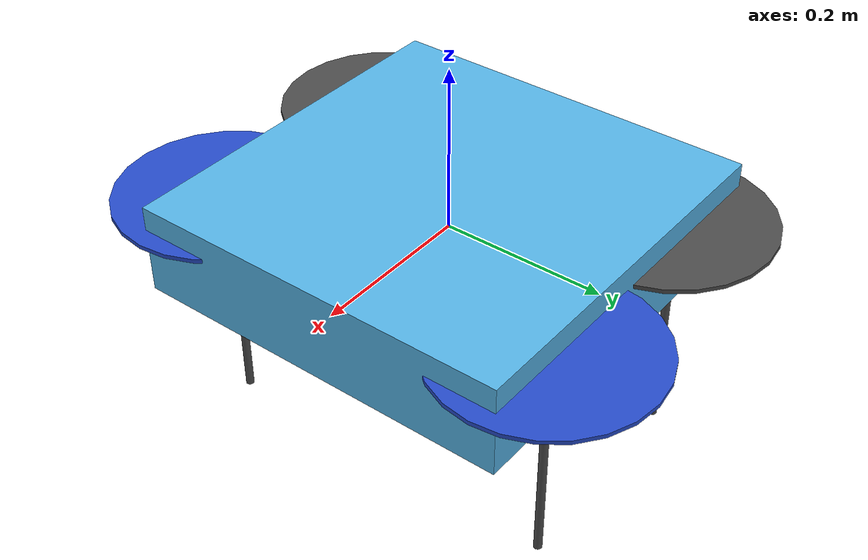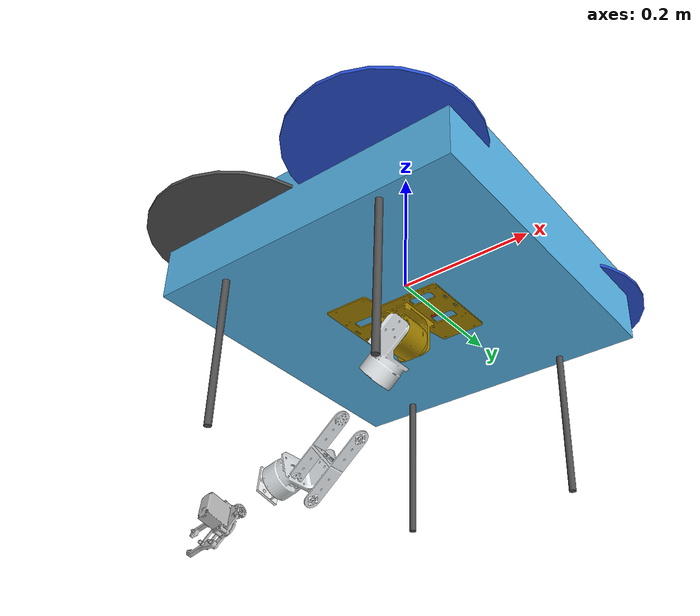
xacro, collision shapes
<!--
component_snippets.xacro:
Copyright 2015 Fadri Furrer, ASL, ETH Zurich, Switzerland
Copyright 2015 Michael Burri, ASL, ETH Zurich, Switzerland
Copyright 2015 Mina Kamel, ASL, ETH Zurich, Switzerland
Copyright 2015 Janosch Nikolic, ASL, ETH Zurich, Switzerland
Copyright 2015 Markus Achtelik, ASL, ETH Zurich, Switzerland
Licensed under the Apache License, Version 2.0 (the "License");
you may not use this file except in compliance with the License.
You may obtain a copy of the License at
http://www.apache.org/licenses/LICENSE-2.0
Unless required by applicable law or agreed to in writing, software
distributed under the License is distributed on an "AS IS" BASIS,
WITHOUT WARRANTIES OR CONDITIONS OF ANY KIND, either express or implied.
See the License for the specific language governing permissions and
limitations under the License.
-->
<?xml version="1.0"?>

<robot name="iris" xmlns:xacro="http://ros.org/wiki/xacro">
  <!-- Properties that can be assigned at build time as arguments.
  Is there a reason not to make all properties arguments?
  -->
  <xacro:arg name='name' default='iris_0' />
  <xacro:arg name='mavlink_addr' default='INADDR_ANY' />
  <xacro:arg name='mavlink_udp_port' default='14560' />
  <xacro:arg name='mavlink_tcp_port' default='4560' />
  <xacro:arg name='serial_enabled' default='false' />
  <xacro:arg name='serial_device' default='/dev/ttyACM0' />
  <xacro:arg name='baudrate' default='921600' />
  <xacro:arg name='qgc_addr' default='INADDR_ANY' />
  <xacro:arg name='qgc_udp_port' default='14550' />
  <xacro:arg name='sdk_addr' default='INADDR_ANY' />
  <xacro:arg name='sdk_udp_port' default='14540' />
  <xacro:arg name='hil_mode' default='false' />
  <xacro:arg name='hil_state_level' default='false' />
  <xacro:arg name='send_vision_estimation' default='false' />
  <xacro:arg name='send_odometry' default='false' />
  <xacro:arg name='enable_lockstep' default='true' />
  <xacro:arg name='use_tcp' default='true' />
  <xacro:arg name='vehicle_is_tailsitter' default='false' />
  <xacro:arg name='visual_material' default='DarkGrey' />
  <xacro:arg name='enable_mavlink_interface' default='true' />
  <xacro:arg name='enable_wind' default='false' />
  <!-- The following causes segfault with multiple vehicles if defaults to true!!! -->
  <xacro:arg name='enable_ground_truth' default='false' />
  <xacro:arg name='enable_cameras' default='true' />
  <xacro:arg name='enable_depth' default='true' />
  <xacro:arg name='enable_logging' default='false' />
  <xacro:arg name='log_file' default='iris' />

  <!-- macros for gazebo plugins, sensors -->
  <xacro:include filename="$(find le_arm)/urdf/component_snippets.xacro" />

  <!-- Instantiate iris "mechanics" -->
  <xacro:include filename="$(find le_arm)/urdf/iris.xacro" />

  <gazebo>
      <plugin name="gazebo_ros_control" filename="libgazebo_ros_control.so">
          <robotNamespace>/</robotNamespace>
      </plugin>

      <plugin name="gazebo_grasp_fix" filename="libgazebo_grasp_fix.so">
          <arm>
            <arm_name>gripper</arm_name>
            <palm_link>base_link</palm_link>
            <gripper_link>left_knuckle_link</gripper_link>
            <gripper_link>right_knuckle_link</gripper_link>
            <gripper_link>left_inner_knuckle_link</gripper_link>
            <gripper_link>left_finger_link</gripper_link>
            <gripper_link>right_inner_knuckle_link</gripper_link>
            <gripper_link>right_finger_link</gripper_link>
          </arm>
      <forces_angle_tolerance>10</forces_angle_tolerance>
      <update_rate>20</update_rate>
      <grip_count_threshold>1</grip_count_threshold>
      <max_grip_count>2</max_grip_count>
      <release_tolerance>0.1</release_tolerance>
      <disable_collisions_on_attach>true</disable_collisions_on_attach>
      <contact_topic>__default_topic__</contact_topic>
     </plugin>
  </gazebo>
  <!-- Instantiate arm "mechanics" -->
  <xacro:include filename="$(find le_arm)/urdf/le_arm.urdf.xacro" />
  <xacro:le_arm parent="base_link" >
    <origin xyz="0 0 0" rpy="-1.5708 0 3.14159"/>
  </xacro:le_arm>

  <xacro:if value="$(arg enable_wind)">
    <xacro:wind_plugin_macro
        namespace="${namespace}"
        wind_direction="0 0 1"
        wind_force_mean="0.7"
        xyz_offset="1 0 0"
        wind_gust_direction="0 0 0"
        wind_gust_duration="0"
        wind_gust_start="0"
        wind_gust_force_mean="0"
        />
  </xacro:if>

  <!-- Instantiate gps plugin. -->
  <xacro:gps_plugin_macro
    namespace="${namespace}"
    gps_noise="true"
    >
  </xacro:gps_plugin_macro>

  <!-- Instantiate magnetometer plugin. -->
  <xacro:magnetometer_plugin_macro
    namespace="${namespace}"
    pub_rate="20"
    noise_density="0.0004"
    random_walk="0.0000064"
    bias_correlation_time="600"
    mag_topic="/mag"
    >
  </xacro:magnetometer_plugin_macro>

  <!-- Instantiate barometer plugin. -->
  <xacro:barometer_plugin_macro
    namespace="${namespace}"
    pub_rate="10"
    baro_topic="/baro"
    >
  </xacro:barometer_plugin_macro>

  <xacro:if value="$(arg enable_mavlink_interface)">
  <!-- Instantiate mavlink telemetry interface. -->
  <xacro:mavlink_interface_macro
    namespace="${namespace}"
    imu_sub_topic="/imu"
    gps_sub_topic="/gps"
    mag_sub_topic="/mag"
    baro_sub_topic="/baro"
    mavlink_addr="$(arg mavlink_addr)"
    mavlink_udp_port="$(arg mavlink_udp_port)"
    mavlink_tcp_port="$(arg mavlink_tcp_port)"
    serial_enabled="$(arg serial_enabled)"
    serial_device="$(arg serial_device)"
    baudrate="$(arg baudrate)"
    qgc_addr="$(arg qgc_addr)"
    qgc_udp_port="$(arg qgc_udp_port)"
    sdk_addr="$(arg sdk_addr)"
    sdk_udp_port="$(arg sdk_udp_port)"
    hil_mode="$(arg hil_mode)"
    hil_state_level="$(arg hil_state_level)"
    vehicle_is_tailsitter="$(arg vehicle_is_tailsitter)"
    send_vision_estimation="$(arg send_vision_estimation)"
    send_odometry="$(arg send_odometry)"
    enable_lockstep="$(arg enable_lockstep)"
    use_tcp="$(arg use_tcp)"
    >
  </xacro:mavlink_interface_macro>
  </xacro:if>

  <!-- Mount an ADIS16448 IMU. -->
  <xacro:imu_plugin_macro
    namespace="${namespace}"
    imu_suffix=""
    parent_link="base_link"
    imu_topic="/imu"
    mass_imu_sensor="0.015"
    gyroscope_noise_density="0.0003394"
    gyroscopoe_random_walk="0.000038785"
    gyroscope_bias_correlation_time="1000.0"
    gyroscope_turn_on_bias_sigma="0.0087"
    accelerometer_noise_density="0.004"
    accelerometer_random_walk="0.006"
    accelerometer_bias_correlation_time="300.0"
    accelerometer_turn_on_bias_sigma="0.1960"
  >
    <inertia ixx="0.00001" ixy="0.0" ixz="0.0" iyy="0.00001" iyz="0.0" izz="0.00001" />
    <origin xyz="0 0 0" rpy="0 0 0" />
  </xacro:imu_plugin_macro>

  <xacro:if value="$(arg enable_ground_truth)">
    <!-- Mount an IMU providing ground truth. -->
    <xacro:imu_plugin_macro
      namespace="${namespace}"
      imu_suffix="gt"
      parent_link="base_link"
      imu_topic="ground_truth/imu"
      mass_imu_sensor="0.00001"
      gyroscope_noise_density="0.0"
      gyroscopoe_random_walk="0.0"
      gyroscope_bias_correlation_time="1000.0"
      gyroscope_turn_on_bias_sigma="0.0"
      accelerometer_noise_density="0.0"
      accelerometer_random_walk="0.0"
      accelerometer_bias_correlation_time="300.0"
      accelerometer_turn_on_bias_sigma="0.0"
    >
      <inertia ixx="0.00001" ixy="0.0" ixz="0.0" iyy="0.00001" iyz="0.0" izz="0.00001" />
      <origin xyz="0 0 0" rpy="0 0 0" />
    </xacro:imu_plugin_macro>

    <!-- Mount a generic odometry sensor providing ground truth. -->
    <xacro:odometry_plugin_macro
      namespace="${namespace}/ground_truth"
      odometry_sensor_suffix="gt"
      parent_link="base_link"
      pose_topic="pose"
      pose_with_covariance_topic="pose_with_covariance"
      position_topic="position"
      transform_topic="transform"
      odometry_topic="odometry"
      parent_frame_id="world"
      mass_odometry_sensor="0.00001"
      measurement_divisor="1"
      measurement_delay="0"
      unknown_delay="0.0"
      noise_normal_position="0 0 0"
      noise_normal_quaternion="0 0 0"
      noise_normal_linear_velocity="0 0 0"
      noise_normal_angular_velocity="0 0 0"
      noise_uniform_position="0 0 0"
      noise_uniform_quaternion="0 0 0"
      noise_uniform_linear_velocity="0 0 0"
      noise_uniform_angular_velocity="0 0 0"
      enable_odometry_map="false"
      odometry_map=""
      image_scale=""
    >
      <inertia ixx="0.00001" ixy="0.0" ixz="0.0" iyy="0.00001" iyz="0.0" izz="0.00001" /> <!-- [kg.m^2] [kg.m^2] [kg.m^2] [kg.m^2] [kg.m^2] [kg.m^2] -->
      <origin xyz="0.0 0.0 0.0" rpy="0.0 0.0 0.0" />
    </xacro:odometry_plugin_macro>
  </xacro:if>

  <xacro:if value="$(arg enable_logging)">
    <!-- Instantiate a logger -->
    <xacro:bag_plugin_macro
      namespace="${namespace}"
      bag_file="$(arg log_file)"
      rotor_velocity_slowdown_sim="${rotor_velocity_slowdown_sim}"
    >
    </xacro:bag_plugin_macro>
  </xacro:if>

  <!-- Instantiate a VI sensor. -->

  <xacro:include filename="$(find le_arm)/urdf/sensors/camera.urdf.xacro"/>

</robot>

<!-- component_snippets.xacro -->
<robot xmlns:xacro="http://ros.org/wiki/xacro">
  <!-- Macro to add logging to a bag file. -->
  <xacro:macro name="bag_plugin_macro"
    params="namespace bag_file rotor_velocity_slowdown_sim">
    <gazebo>
      <plugin filename="librotors_gazebo_bag_plugin.so" name="rosbag">
        <robotNamespace>${namespace}</robotNamespace>
        <bagFileName>${bag_file}</bagFileName>
        <linkName>base_link</linkName>
        <frameId>base_link</frameId>
        <commandAttitudeThrustSubTopic>command/attitude</commandAttitudeThrustSubTopic>
        <commandAttitudeThrustPubTopic>command/attitude</commandAttitudeThrustPubTopic>
        <rotorVelocitySlowdownSim>${rotor_velocity_slowdown_sim}</rotorVelocitySlowdownSim>
      </plugin>
    </gazebo>
  </xacro:macro>

  <!-- Macro to add a camera. -->
  <xacro:macro name="camera_macro"
    params="namespace parent_link camera_suffix frame_rate
      horizontal_fov image_width image_height image_format min_distance
      max_distance noise_mean noise_stddev enable_visual *cylinder *origin">
    <link name="${namespace}/camera_${camera_suffix}_link">
      <collision>
        <origin xyz="0 0 0" rpy="0 0 0" />
        <geometry>
          <xacro:insert_block name="cylinder" />
        </geometry>
      </collision>
      <xacro:if value="${enable_visual}">
        <visual>
          <origin xyz="0 0 0" rpy="0 1.57079632679 0" />
          <geometry>
            <xacro:insert_block name="cylinder" />
          </geometry>
          <material name="red" />
        </visual>
      </xacro:if>
      <inertial>
        <mass value="1e-5" />
        <origin xyz="0 0 0" rpy="0 0 0" />
        <inertia ixx="1e-6" ixy="0" ixz="0" iyy="1e-6" iyz="0" izz="1e-6" />
      </inertial>
    </link>
    <joint name="${namespace}/camera_${camera_suffix}_joint" type="fixed">
      <xacro:insert_block name="origin" />
      <parent link="${parent_link}" />
      <child link="${namespace}/camera_${camera_suffix}_link" />
    </joint>
    <gazebo reference="${namespace}/camera_${camera_suffix}_link">
      <sensor type="camera" name="${namespace}_camera_${camera_suffix}">
        <update_rate>${frame_rate}</update_rate>
        <camera name="head">
          <horizontal_fov>${horizontal_fov}</horizontal_fov>
          <image>
            <width>${image_width}</width>
            <height>${image_height}</height>
            <format>${image_format}</format>
          </image>
          <clip>
            <near>${min_distance}</near>
            <far>${max_distance}</far>
          </clip>
          <noise>
            <type>gaussian</type>
            <!-- Noise is sampled independently per pixel on each frame.
                 That pixel's noise value is added to each of its color
                 channels, which at that point lie in the range [0,1]. -->
            <mean>${noise_mean}</mean>
            <stddev>${noise_stddev}</stddev>
          </noise>
        </camera>
        <plugin name="${namespace}_camera_${camera_suffix}_controller" filename="libgazebo_ros_camera.so">
          <robotNamespace>${namespace}</robotNamespace>
          <alwaysOn>true</alwaysOn>
          <updateRate>${frame_rate}</updateRate>
          <cameraName>${camera_suffix}</cameraName>
          <imageTopicName>image_raw</imageTopicName>
          <cameraInfoTopicName>camera_info</cameraInfoTopicName>
          <frameName>camera_${camera_suffix}_link</frameName>
          <hackBaseline>0.0</hackBaseline>
          <distortionK1>0.0</distortionK1>
          <distortionK2>0.0</distortionK2>
          <distortionK3>0.0</distortionK3>
          <distortionT1>0.0</distortionT1>
          <distortionT2>0.0</distortionT2>
        </plugin>
      </sensor>
    </gazebo>
  </xacro:macro>

  <!-- Macro to add the controller interface. -->
  <xacro:macro name="controller_plugin_macro" params="namespace imu_sub_topic">
    <gazebo>
      <plugin name="controller_interface" filename="libgazebo_controller_interface.so">
        <robotNamespace>${namespace}</robotNamespace>
        <commandAttitudeThrustSubTopic>/command/attitude</commandAttitudeThrustSubTopic>
        <commandRateThrustSubTopic>/command/rate</commandRateThrustSubTopic>
        <commandMotorSpeedSubTopic>/command/motor_speed</commandMotorSpeedSubTopic>
        <imuSubTopic>/${imu_sub_topic}</imuSubTopic>
        <motorSpeedCommandPubTopic>/gazebo/command/motor_speed</motorSpeedCommandPubTopic>
      </plugin>
    </gazebo>
  </xacro:macro>

  <!-- Macro to add the gps_plugin. -->
  <xacro:macro name="gps_plugin_macro" params="namespace gps_noise">
    <gazebo>
      <plugin name="gps_plugin" filename="libgazebo_gps_plugin.so">
        <robotNamespace>${namespace}</robotNamespace>
        <gpsNoise>${gps_noise}</gpsNoise>
      </plugin>
    </gazebo>
  </xacro:macro>

  <!-- Macro to add the magnetometer_plugin. -->
  <xacro:macro name="magnetometer_plugin_macro" params="namespace pub_rate noise_density random_walk bias_correlation_time mag_topic">
    <gazebo>
      <plugin name="magnetometer_plugin" filename="libgazebo_magnetometer_plugin.so">
        <robotNamespace>${namespace}</robotNamespace>
        <pubRate>${pub_rate}</pubRate>
        <noiseDensity>${noise_density}</noiseDensity>
        <randomWalk>${random_walk}</randomWalk>
        <biasCorrelationTime>${bias_correlation_time}</biasCorrelationTime>
        <magTopic>${mag_topic}</magTopic>
      </plugin>
    </gazebo>
  </xacro:macro>

  <!-- Macro to add the barometer_plugin. -->
  <xacro:macro name="barometer_plugin_macro" params="namespace pub_rate baro_topic">
    <gazebo>
      <plugin name="barometer_plugin" filename="libgazebo_barometer_plugin.so">
        <robotNamespace>${namespace}</robotNamespace>
        <pubRate>${pub_rate}</pubRate>
        <baroTopic>${baro_topic}</baroTopic>
      </plugin>
    </gazebo>
  </xacro:macro>

  <!-- Macro to add the mavlink interface. -->
  <xacro:macro name="mavlink_interface_macro" params="namespace imu_sub_topic gps_sub_topic mag_sub_topic baro_sub_topic mavlink_addr mavlink_udp_port mavlink_tcp_port serial_enabled serial_device baudrate qgc_addr qgc_udp_port sdk_addr sdk_udp_port hil_mode hil_state_level vehicle_is_tailsitter send_vision_estimation send_odometry enable_lockstep use_tcp">
    <gazebo>
      <plugin name="mavlink_interface" filename="libgazebo_mavlink_interface.so">
        <robotNamespace>${namespace}</robotNamespace>
        <imuSubTopic>${imu_sub_topic}</imuSubTopic>
        <gpsSubTopic>${gps_sub_topic}</gpsSubTopic>
        <magSubTopic>${mag_sub_topic}</magSubTopic>
        <baroSubTopic>${baro_sub_topic}</baroSubTopic>
        <mavlink_addr>$(arg mavlink_addr)</mavlink_addr>
        <mavlink_udp_port>$(arg mavlink_udp_port)</mavlink_udp_port>
        <mavlink_tcp_port>$(arg mavlink_tcp_port)</mavlink_tcp_port>
        <serialEnabled>$(arg serial_enabled)</serialEnabled>
        <serialDevice>$(arg serial_device)</serialDevice>
        <baudRate>$(arg baudrate)</baudRate>
        <qgc_addr>$(arg qgc_addr)</qgc_addr>
        <qgc_udp_port>$(arg qgc_udp_port)</qgc_udp_port>
        <sdk_addr>$(arg sdk_addr)</sdk_addr>
        <sdk_udp_port>$(arg sdk_udp_port)</sdk_udp_port>
        <hil_mode>$(arg hil_mode)</hil_mode>
        <hil_state_level>$(arg hil_state_level)</hil_state_level>
        <vehicle_is_tailsitter>$(arg vehicle_is_tailsitter)</vehicle_is_tailsitter>
        <send_vision_estimation>$(arg send_vision_estimation)</send_vision_estimation>
        <send_odometry>$(arg send_odometry)</send_odometry>
        <enable_lockstep>$(arg enable_lockstep)</enable_lockstep>
        <use_tcp>$(arg use_tcp)</use_tcp>
        <motorSpeedCommandPubTopic>/gazebo/command/motor_speed</motorSpeedCommandPubTopic>
        <control_channels>
          <channel name="rotor1">
            <input_index>0</input_index>
            <input_offset>0</input_offset>
            <input_scaling>1000</input_scaling>
            <zero_position_disarmed>0</zero_position_disarmed>
            <zero_position_armed>100</zero_position_armed>
            <joint_control_type>velocity</joint_control_type>
          </channel>
          <channel name="rotor2">
            <input_index>1</input_index>
            <input_offset>0</input_offset>
            <input_scaling>1000</input_scaling>
            <zero_position_disarmed>0</zero_position_disarmed>
            <zero_position_armed>100</zero_position_armed>
            <joint_control_type>velocity</joint_control_type>
          </channel>
          <channel name="rotor3">
            <input_index>2</input_index>
            <input_offset>0</input_offset>
            <input_scaling>1000</input_scaling>
            <zero_position_disarmed>0</zero_position_disarmed>
            <zero_position_armed>100</zero_position_armed>
            <joint_control_type>velocity</joint_control_type>
          </channel>
          <channel name="rotor4">
            <input_index>3</input_index>
            <input_offset>0</input_offset>
            <input_scaling>1000</input_scaling>
            <zero_position_disarmed>0</zero_position_disarmed>
            <zero_position_armed>100</zero_position_armed>
            <joint_control_type>velocity</joint_control_type>
          </channel>
          <channel name="rotor5">
            <input_index>4</input_index>
            <input_offset>1</input_offset>
            <input_scaling>324.6</input_scaling>
            <zero_position_disarmed>0</zero_position_disarmed>
            <zero_position_armed>0</zero_position_armed>
            <joint_control_type>velocity</joint_control_type>
            <joint_control_pid>
              <p>0.1</p>
              <i>0</i>
              <d>0</d>
              <iMax>0.0</iMax>
              <iMin>0.0</iMin>
              <cmdMax>2</cmdMax>
              <cmdMin>-2</cmdMin>
            </joint_control_pid>
            <joint_name>zephyr_delta_wing::propeller_joint</joint_name>
          </channel>
          <channel name="rotor6">
            <input_index>5</input_index>
            <input_offset>0</input_offset>
            <!-- joint limits [-0.524, 0.524] -->
            <input_scaling>0.524</input_scaling>
            <zero_position_disarmed>0</zero_position_disarmed>
            <zero_position_armed>0</zero_position_armed>
            <joint_control_type>position</joint_control_type>
            <joint_name>zephyr_delta_wing::flap_left_joint</joint_name>
            <joint_control_pid>
              <p>10.0</p>
              <i>0</i>
              <d>0</d>
              <iMax>0</iMax>
              <iMin>0</iMin>
              <cmdMax>20</cmdMax>
              <cmdMin>-20</cmdMin>
            </joint_control_pid>
          </channel>
          <channel name="rotor7">
            <input_index>6</input_index>
            <input_offset>0</input_offset>
            <!-- joint limits [-0.524, 0.524] -->
            <input_scaling>0.524</input_scaling>
            <zero_position_disarmed>0</zero_position_disarmed>
            <zero_position_armed>0</zero_position_armed>
            <joint_control_type>position</joint_control_type>
            <joint_name>zephyr_delta_wing::flap_right_joint</joint_name>
            <joint_control_pid>
              <p>10.0</p>
              <i>0</i>
              <d>0</d>
              <iMax>0</iMax>
              <iMin>0</iMin>
              <cmdMax>20</cmdMax>
              <cmdMin>-20</cmdMin>
            </joint_control_pid>
          </channel>
          <channel name="rotor8">
            <input_index>7</input_index>
            <input_offset>0</input_offset>
            <input_scaling>0.524</input_scaling>
            <zero_position_disarmed>0</zero_position_disarmed>
            <zero_position_armed>0</zero_position_armed>
            <joint_control_type>position</joint_control_type>
          </channel>
        </control_channels>
      </plugin>
    </gazebo>
  </xacro:macro>

  <!-- Macro to add the mavlink interface for a fixed-wing model. -->
  <xacro:macro name="mavlink_interface_macro_fw" params="namespace imu_sub_topic gps_sub_topic mag_sub_topic baro_sub_topic mavlink_addr mavlink_udp_port mavlink_tcp_port serial_enabled serial_device baudrate qgc_addr qgc_udp_port sdk_addr sdk_udp_port hil_mode hil_state_level vehicle_is_tailsitter send_vision_estimation send_odometry enable_lockstep use_tcp">
    <gazebo>
      <plugin name="mavlink_interface" filename="libgazebo_mavlink_interface.so">
        <robotNamespace>${namespace}</robotNamespace>
        <imuSubTopic>${imu_sub_topic}</imuSubTopic>
        <gpsSubTopic>${gps_sub_topic}</gpsSubTopic>
        <magSubTopic>${mag_sub_topic}</magSubTopic>
        <baroSubTopic>${baro_sub_topic}</baroSubTopic>
        <mavlink_addr>$(arg mavlink_addr)</mavlink_addr>
        <mavlink_udp_port>$(arg mavlink_udp_port)</mavlink_udp_port>
        <mavlink_tcp_port>$(arg mavlink_tcp_port)</mavlink_tcp_port>
        <serialEnabled>$(arg serial_enabled)</serialEnabled>
        <serialDevice>$(arg serial_device)</serialDevice>
        <baudRate>$(arg baudrate)</baudRate>
        <qgc_addr>$(arg qgc_addr)</qgc_addr>
        <qgc_udp_port>$(arg qgc_udp_port)</qgc_udp_port>
        <sdk_addr>$(arg sdk_addr)</sdk_addr>
        <sdk_udp_port>$(arg sdk_udp_port)</sdk_udp_port>
        <hil_mode>$(arg hil_mode)</hil_mode>
        <hil_state_level>$(arg hil_state_level)</hil_state_level>
        <vehicle_is_tailsitter>$(arg vehicle_is_tailsitter)</vehicle_is_tailsitter>
        <send_vision_estimation>$(arg send_vision_estimation)</send_vision_estimation>
        <send_odometry>$(arg send_odometry)</send_odometry>
        <enable_lockstep>$(arg enable_lockstep)</enable_lockstep>
        <use_tcp>$(arg use_tcp)</use_tcp>
        <motorSpeedCommandPubTopic>/gazebo/command/motor_speed</motorSpeedCommandPubTopic>
        <control_channels>
          <channel name="rudder">
            <input_index>2</input_index>
            <input_offset>0</input_offset>
            <input_scaling>1</input_scaling>
            <zero_position_disarmed>0</zero_position_disarmed>
            <zero_position_armed>0</zero_position_armed>
            <joint_control_type>position_kinematic</joint_control_type>
            <joint_name>rudder_joint</joint_name>
          </channel>
          <channel name="rotor_4">
            <input_index>4</input_index>
            <input_offset>0</input_offset>
            <input_scaling>3500</input_scaling>
            <zero_position_disarmed>0</zero_position_disarmed>
            <zero_position_armed>0</zero_position_armed>
            <joint_control_type>velocity</joint_control_type>
            <joint_name>rotor_4_joint</joint_name>
          </channel>
          <channel name="left_aileron">
            <input_index>5</input_index>
            <input_offset>0</input_offset>
            <input_scaling>1</input_scaling>
            <zero_position_disarmed>0</zero_position_disarmed>
            <zero_position_armed>0</zero_position_armed>
            <joint_control_type>position_kinematic</joint_control_type>
            <joint_name>left_elevon_joint</joint_name>
          </channel>
          <channel name="right_aileron">
            <input_index>6</input_index>
            <input_offset>0</input_offset>
            <input_scaling>1</input_scaling>
            <zero_position_disarmed>0</zero_position_disarmed>
            <zero_position_armed>0</zero_position_armed>
            <joint_control_type>position_kinematic</joint_control_type>
            <joint_name>right_elevon_joint</joint_name>
          </channel>
          <channel name="elevator">
            <input_index>7</input_index>
            <input_offset>0</input_offset>
            <input_scaling>1</input_scaling>
            <zero_position_disarmed>0</zero_position_disarmed>
            <zero_position_armed>0</zero_position_armed>
            <joint_control_type>position_kinematic</joint_control_type>
            <joint_name>elevator_joint</joint_name>
          </channel>
        </control_channels>
      </plugin>
    </gazebo>
  </xacro:macro>

  <!-- Macro to add the mavlink interface for a fixed-wing model. -->
  <xacro:macro name="mavlink_interface_macro_vtol" params="namespace imu_sub_topic gps_sub_topic mag_sub_topic baro_sub_topic mavlink_addr mavlink_udp_port mavlink_tcp_port serial_enabled serial_device baudrate qgc_addr qgc_udp_port sdk_addr sdk_udp_port hil_mode hil_state_level vehicle_is_tailsitter send_vision_estimation send_odometry enable_lockstep use_tcp">
    <gazebo>
      <plugin name='mavlink_interface' filename='libgazebo_mavlink_interface.so'>
        <robotNamespace>${namespace}</robotNamespace>
        <imuSubTopic>${imu_sub_topic}</imuSubTopic>
        <gpsSubTopic>${gps_sub_topic}</gpsSubTopic>
        <magSubTopic>${mag_sub_topic}</magSubTopic>
        <baroSubTopic>${baro_sub_topic}</baroSubTopic>
        <mavlink_addr>$(arg mavlink_addr)</mavlink_addr>
        <mavlink_udp_port>$(arg mavlink_udp_port)</mavlink_udp_port>
        <mavlink_tcp_port>$(arg mavlink_tcp_port)</mavlink_tcp_port>
        <serialEnabled>$(arg serial_enabled)</serialEnabled>
        <serialDevice>$(arg serial_device)</serialDevice>
        <baudRate>$(arg baudrate)</baudRate>
        <qgc_addr>$(arg qgc_addr)</qgc_addr>
        <qgc_udp_port>$(arg qgc_udp_port)</qgc_udp_port>
        <sdk_addr>$(arg sdk_addr)</sdk_addr>
        <sdk_udp_port>$(arg sdk_udp_port)</sdk_udp_port>
        <hil_mode>$(arg hil_mode)</hil_mode>
        <hil_state_level>$(arg hil_state_level)</hil_state_level>
        <vehicle_is_tailsitter>$(arg vehicle_is_tailsitter)</vehicle_is_tailsitter>
        <send_vision_estimation>$(arg send_vision_estimation)</send_vision_estimation>
        <send_odometry>$(arg send_odometry)</send_odometry>
        <enable_lockstep>$(arg enable_lockstep)</enable_lockstep>
        <use_tcp>$(arg use_tcp)</use_tcp>
        <motorSpeedCommandPubTopic>/gazebo/command/motor_speed</motorSpeedCommandPubTopic>
        <control_channels>
          <channel name="rotor0">
            <input_index>0</input_index>
            <input_offset>0</input_offset>
            <input_scaling>1500</input_scaling>
            <zero_position_disarmed>0</zero_position_disarmed>
            <zero_position_armed>0</zero_position_armed>
            <joint_control_type>velocity</joint_control_type>
            <joint_name>rotor_0_joint</joint_name>
          </channel>
          <channel name="rotor1">
            <input_index>1</input_index>
            <input_offset>0</input_offset>
            <input_scaling>1500</input_scaling>
            <zero_position_disarmed>0</zero_position_disarmed>
            <zero_position_armed>0</zero_position_armed>
            <joint_control_type>velocity</joint_control_type>
            <joint_name>rotor_1_joint</joint_name>
          </channel>
          <channel name="rotor2">
            <input_index>2</input_index>
            <input_offset>0</input_offset>
            <input_scaling>1500</input_scaling>
            <zero_position_disarmed>0</zero_position_disarmed>
            <zero_position_armed>0</zero_position_armed>
            <joint_control_type>velocity</joint_control_type>
            <joint_name>rotor_2_joint</joint_name>
          </channel>
          <channel name="rotor3">
            <input_index>3</input_index>
            <input_offset>0</input_offset>
            <input_scaling>1500</input_scaling>
            <zero_position_disarmed>0</zero_position_disarmed>
            <zero_position_armed>0</zero_position_armed>
            <joint_control_type>velocity</joint_control_type>
            <joint_name>rotor_3_joint</joint_name>
          </channel>
          <channel name="rotor4">
            <input_index>4</input_index>
            <input_offset>0</input_offset>
            <input_scaling>5500</input_scaling>
            <zero_position_disarmed>0</zero_position_disarmed>
            <zero_position_armed>0</zero_position_armed>
            <joint_control_type>velocity</joint_control_type>
            <joint_name>rotor_puller_joint</joint_name>
          </channel>
          <channel name="left_elevon">
            <input_index>5</input_index>
            <input_offset>0</input_offset>
            <input_scaling>1</input_scaling>
            <zero_position_disarmed>0</zero_position_disarmed>
            <zero_position_armed>0</zero_position_armed>
            <joint_control_type>position_kinematic</joint_control_type>
            <joint_name>left_elevon_joint</joint_name>
          </channel>
          <channel name="right_elevon">
            <input_index>6</input_index>
            <input_offset>0</input_offset>
            <input_scaling>1</input_scaling>
            <zero_position_disarmed>0</zero_position_disarmed>
            <zero_position_armed>0</zero_position_armed>
            <joint_control_type>position_kinematic</joint_control_type>
            <joint_name>right_elevon_joint</joint_name>
          </channel>
          <channel name="elevator">
            <input_index>7</input_index>
            <input_offset>0</input_offset>
            <input_scaling>1</input_scaling>
            <zero_position_disarmed>0</zero_position_disarmed>
            <zero_position_armed>0</zero_position_armed>
            <joint_control_type>position_kinematic</joint_control_type>
            <joint_name>elevator_joint</joint_name>
          </channel>
        </control_channels>
        <left_elevon_joint>
          left_elevon_joint
        </left_elevon_joint>
        <right_elevon_joint>
          right_elevon_joint
        </right_elevon_joint>
        <elevator_joint>
          elevator_joint
        </elevator_joint>
      </plugin>
    </gazebo>
  </xacro:macro>

  <!-- Macro to add an IMU. -->
  <xacro:macro name="imu_plugin_macro"
    params="namespace imu_suffix parent_link imu_topic
      mass_imu_sensor gyroscope_noise_density gyroscopoe_random_walk
      gyroscope_bias_correlation_time gyroscope_turn_on_bias_sigma
      accelerometer_noise_density accelerometer_random_walk
      accelerometer_bias_correlation_time accelerometer_turn_on_bias_sigma
      *inertia *origin">
    <!-- IMU link -->
    <link name="${namespace}/imu${imu_suffix}_link">
      <inertial>
        <xacro:insert_block name="inertia" />
        <mass value="${mass_imu_sensor}" />  <!-- [kg] -->
        <origin xyz="0 0 0" rpy="0 0 0" />
      </inertial>
    </link>
    <!-- IMU joint -->
    <joint name="${namespace}/imu${imu_suffix}_joint" type="revolute">
      <xacro:insert_block name="origin" />
      <parent link="${parent_link}" />
      <child link="${namespace}/imu${imu_suffix}_link" />
      <limit upper="0" lower="0" effort="0" velocity="0" />
    </joint>
    <gazebo>
      <plugin filename="libgazebo_imu_plugin.so" name="rotors_gazebo_imu${imu_suffix}_plugin">
      <!-- A good description of the IMU parameters can be found in the kalibr documentation:
           https://github.com/ethz-asl/kalibr/wiki/IMU-Noise-Model-and-Intrinsics -->
        <robotNamespace>${namespace}</robotNamespace> <!-- (string, required): ros namespace in which the messages are published -->
        <linkName>${namespace}/imu${imu_suffix}_link</linkName> <!-- (string, required): name of the body which holds the IMU sensor -->
        <imuTopic>${imu_topic}</imuTopic> <!-- (string): name of the sensor output topic and prefix of service names (defaults to imu) -->
        <gyroscopeNoiseDensity>${gyroscope_noise_density}</gyroscopeNoiseDensity> <!-- Gyroscope noise density (two-sided spectrum) [rad/s/sqrt(Hz)] -->
        <gyroscopeRandomWalk>${gyroscopoe_random_walk}</gyroscopeRandomWalk> <!-- Gyroscope bias random walk [rad/s/s/sqrt(Hz)] -->
        <gyroscopeBiasCorrelationTime>${gyroscope_bias_correlation_time}</gyroscopeBiasCorrelationTime> <!-- Gyroscope bias correlation time constant [s] -->
        <gyroscopeTurnOnBiasSigma>${gyroscope_turn_on_bias_sigma}</gyroscopeTurnOnBiasSigma> <!-- Gyroscope turn on bias standard deviation [rad/s] -->
        <accelerometerNoiseDensity>${accelerometer_noise_density}</accelerometerNoiseDensity> <!-- Accelerometer noise density (two-sided spectrum) [m/s^2/sqrt(Hz)] -->
        <accelerometerRandomWalk>${accelerometer_random_walk}</accelerometerRandomWalk> <!-- Accelerometer bias random walk. [m/s^2/s/sqrt(Hz)] -->
        <accelerometerBiasCorrelationTime>${accelerometer_bias_correlation_time}</accelerometerBiasCorrelationTime> <!-- Accelerometer bias correlation time constant [s] -->
        <accelerometerTurnOnBiasSigma>${accelerometer_turn_on_bias_sigma}</accelerometerTurnOnBiasSigma> <!-- Accelerometer turn on bias standard deviation [m/s^2] -->
      </plugin>
    </gazebo>
  </xacro:macro>

<!-- Macro to add a generic odometry sensor. -->
  <xacro:macro name="odometry_plugin_macro"
    params="
      namespace odometry_sensor_suffix parent_link pose_topic pose_with_covariance_topic
      position_topic transform_topic odometry_topic parent_frame_id
      mass_odometry_sensor measurement_divisor measurement_delay unknown_delay
      noise_normal_position noise_normal_quaternion noise_normal_linear_velocity
      noise_normal_angular_velocity noise_uniform_position
      noise_uniform_quaternion noise_uniform_linear_velocity
      noise_uniform_angular_velocity enable_odometry_map odometry_map
      image_scale *inertia *origin">
    <!-- odometry link -->
    <link name="${namespace}/odometry_sensor${odometry_sensor_suffix}_link">
      <inertial>
        <xacro:insert_block name="inertia" />
        <mass value="${mass_odometry_sensor}" />  <!-- [kg] -->
      </inertial>
    </link>
    <!-- odometry joint -->
    <joint name="${namespace}/odometry_sensor${odometry_sensor_suffix}_joint" type="revolute">
      <parent link="${parent_link}" />
      <xacro:insert_block name="origin" />
      <child link="${namespace}/odometry_sensor${odometry_sensor_suffix}_link" />
      <limit upper="0" lower="0" effort="0" velocity="0" />
    </joint>
    <gazebo>
      <plugin filename="librotors_gazebo_odometry_plugin.so" name="odometry_sensor${odometry_sensor_suffix}">
        <linkName>${namespace}/odometry_sensor${odometry_sensor_suffix}_link</linkName>
        <robotNamespace>${namespace}</robotNamespace>
        <poseTopic>${pose_topic}</poseTopic>
        <poseWithCovarianceTopic>${pose_with_covariance_topic}</poseWithCovarianceTopic>
        <positionTopic>${position_topic}</positionTopic>
        <transformTopic>${transform_topic}</transformTopic>
        <odometryTopic>${odometry_topic}</odometryTopic>
        <parentFrameId>${parent_frame_id}</parentFrameId>  <!-- Use the scoped link name here. e.g. Model::link. -->
        <measurementDivisor>${measurement_divisor}</measurementDivisor> <!-- only every (seq % measurementDivisor) == 0 measurement is published [int] -->
        <measurementDelay>${measurement_delay}</measurementDelay> <!-- time that measurement gets held back before it's published in [simulation cycles (int)] -->
        <unknownDelay>${unknown_delay}</unknownDelay> <!-- additional delay, that just gets added to the timestamp [s] -->
        <noiseNormalPosition>${noise_normal_position}</noiseNormalPosition> <!-- standard deviation of additive white gaussian noise [m] -->
        <noiseNormalQuaternion>${noise_normal_quaternion}</noiseNormalQuaternion> <!-- standard deviation white gaussian noise [rad]: q_m = q*quaternionFromSmallAngleApproximation(noiseNormalQ) -->
        <noiseNormalLinearVelocity>${noise_normal_linear_velocity}</noiseNormalLinearVelocity> <!-- standard deviation of additive white gaussian noise [m/s] -->
        <noiseNormalAngularVelocity>${noise_normal_angular_velocity}</noiseNormalAngularVelocity> <!-- standard deviation of additive white gaussian noise [rad/s] -->
        <noiseUniformPosition>${noise_uniform_position}</noiseUniformPosition> <!-- symmetric bounds of uniform noise [m] -->
        <noiseUniformQuaternion>${noise_uniform_quaternion}</noiseUniformQuaternion> <!-- symmetric bounds of uniform noise [rad], computation see above -->
        <noiseUniformLinearVelocity>${noise_uniform_linear_velocity}</noiseUniformLinearVelocity>  <!-- symmetric bounds of uniform noise [m/s] -->
        <noiseUniformAngularVelocity>${noise_uniform_angular_velocity}</noiseUniformAngularVelocity>  <!-- symmetric bounds of uniform noise [rad/s] -->
        <xacro:if value="${enable_odometry_map}">
          <covarianceImage>package://rotors_gazebo/resource/${odometry_map}</covarianceImage>
          <covarianceImageScale>${image_scale}</covarianceImageScale>
        </xacro:if>
      </plugin>
    </gazebo>
  </xacro:macro>

  <!-- Macro to add the wind plugin. -->
  <xacro:macro name="wind_plugin_macro"
    params="namespace xyz_offset wind_direction wind_force_mean
      wind_gust_direction wind_gust_duration wind_gust_start
      wind_gust_force_mean">
    <gazebo>
      <plugin filename="libgazebo_wind_plugin.so" name="wind_plugin">
        <frameId>base_link</frameId>
        <linkName>base_link</linkName>
        <robotNamespace>${namespace}</robotNamespace>
        <xyzOffset>${xyz_offset}</xyzOffset>
        <windDirection>${wind_direction}</windDirection>
        <windForceMean>${wind_force_mean}</windForceMean>
        <windGustDirection>${wind_gust_direction}</windGustDirection>
        <windGustDuration>${wind_gust_duration}</windGustDuration>
        <windGustStart>${wind_gust_start}</windGustStart>
        <windGustForceMean>${wind_gust_force_mean}</windGustForceMean>
      </plugin>
    </gazebo>
  </xacro:macro>

  <!-- VI sensor macros -->
  <!-- Macro to add a VI-sensor camera. -->
  <xacro:macro name="vi_sensor_camera_macro"
    params="namespace parent_link camera_suffix frame_rate *origin">
    <xacro:camera_macro
      namespace="${namespace}"
      parent_link="${parent_link}"
      camera_suffix="${camera_suffix}"
      frame_rate="${frame_rate}"
      horizontal_fov="1.3962634"
      image_width="752"
      image_height="480"
      image_format="L8"
      min_distance="0.02"
      max_distance="30"
      noise_mean="0.0"
      noise_stddev="0.007"
      enable_visual="false">
      <cylinder length="0.01" radius="0.007" />
      <xacro:insert_block name="origin" />
    </xacro:camera_macro>
  </xacro:macro>

  <!-- Macro to add a depth camera on the VI-sensor. -->
  <xacro:macro name="vi_sensor_depth_macro"
    params="namespace parent_link camera_suffix frame_rate *origin">
    <link name="${namespace}/camera_${camera_suffix}_link">
      <collision>
        <origin xyz="0 0 0" rpy="0 0 0" />
        <geometry>
          <cylinder length="0.01" radius="0.007" />
        </geometry>
      </collision>
      <inertial>
        <mass value="1e-5" />
        <origin xyz="0 0 0" rpy="0 0 0" />
        <inertia ixx="1e-6" ixy="0" ixz="0" iyy="1e-6" iyz="0" izz="1e-6" />
      </inertial>
    </link>
    <joint name="${namespace}/camera_${camera_suffix}_joint" type="fixed">
      <xacro:insert_block name="origin" />
      <parent link="${parent_link}" />
      <child link="${namespace}/camera_${camera_suffix}_link" />
      <limit upper="0" lower="0" effort="0" velocity="0" />
    </joint>
    <!-- Optical center of camera -->
    <link name="${namespace}/camera_${camera_suffix}_optical_center_link" />
    <joint name="${namespace}/camera_${camera_suffix}_optical_center_joint" type="fixed">
      <origin xyz="0 0 0" rpy="-1.57 0 -1.57" />
      <parent link="${namespace}/camera_${camera_suffix}_link" />
      <child link="${namespace}/camera_${camera_suffix}_optical_center_link" />
      <limit upper="0" lower="0" effort="0" velocity="0" />
    </joint>
    <gazebo reference="${namespace}/camera_${camera_suffix}_link">
      <sensor type="depth" name="${namespace}_camera_{camera_suffix}">
        <always_on>true</always_on>
        <update_rate>${frame_rate}</update_rate>
        <camera>
          <horizontal_fov>2</horizontal_fov>
          <image>
            <format>L8</format>
            <width>640</width>
            <height>480</height>
          </image>
          <clip>
            <near>0.01</near>
            <far>100</far>
          </clip>
        </camera>
        <plugin name="${namespace}_camera_{camera_suffix}" filename="libgazebo_ros_openni_kinect.so">
          <robotNamespace>${namespace}</robotNamespace>
          <alwaysOn>true</alwaysOn>
          <baseline>0.11</baseline>
          <updateRate>${frame_rate}</updateRate>
          <cameraName>camera_${camera_suffix}</cameraName>
          <imageTopicName>camera/image_raw</imageTopicName>
          <cameraInfoTopicName>camera/camera_info</cameraInfoTopicName>
          <depthImageTopicName>depth/disparity</depthImageTopicName>
          <depthImageCameraInfoTopicName>depth/camera_info</depthImageCameraInfoTopicName>
          <pointCloudTopicName>depth/points</pointCloudTopicName>
          <frameName>camera_${camera_suffix}_optical_center_link</frameName>
          <pointCloudCutoff>0.5</pointCloudCutoff>
          <distortionK1>0.0</distortionK1>
          <distortionK2>0.0</distortionK2>
          <distortionK3>0.0</distortionK3>
          <distortionT1>0.0</distortionT1>
          <distortionT2>0.0</distortionT2>
        </plugin>
      </sensor>
    </gazebo>
  </xacro:macro>

  <!-- VI-Sensor Macro -->
  <xacro:macro name="vi_sensor_macro" params="namespace parent_link *origin">
    <!-- Vi Sensor Link -->
    <link name="${namespace}/vi_sensor_link">
      <collision>
        <origin xyz="0 0 0" rpy="0 0 0" />
        <geometry>
         <box size="0.015 0.1 0.02" />
        </geometry>
      </collision>

      <visual>
        <origin xyz="0 0 0" rpy="0 0 0" />
        <geometry>
          <box size="0.015 0.1 0.02" />
        </geometry>
      </visual>

      <inertial>
        <mass value="0.13" />
        <origin xyz="0 0 0" rpy="0 0 0" />
        <inertia ixx="1e-6" ixy="0" ixz="0" iyy="1e-6" iyz="0" izz="1e-6" />
      </inertial>
    </link>
    <joint name="{namespace}_vi_sensor_joint" type="fixed">
      <xacro:insert_block name="origin" />
      <parent link="${parent_link}" />
      <child link="${namespace}/vi_sensor_link" />
    </joint>
    <!-- Cameras -->
    <xacro:if value="$(arg enable_cameras)">
      <!-- Left Camera -->
      <xacro:vi_sensor_camera_macro
        namespace="${namespace}/stereo_camera" parent_link="${namespace}/vi_sensor_link"
        camera_suffix="left" frame_rate="30.0">
        <origin xyz="0.015 0.055 0.0065" rpy="0 0 0" />
      </xacro:vi_sensor_camera_macro>
      <!-- Right Camera -->
      <xacro:vi_sensor_camera_macro namespace="${namespace}/stereo_camera"
        parent_link="${namespace}/vi_sensor_link"
        camera_suffix="right" frame_rate="30.0">
        <origin xyz="0.015 -0.055 0.0065" rpy="0 0 0" />
      </xacro:vi_sensor_camera_macro>
    </xacro:if>

    <!-- Depth Sensor -->
    <xacro:if value="$(arg enable_depth)">
      <xacro:vi_sensor_depth_macro
        namespace="${namespace}" parent_link="${namespace}/vi_sensor_link"
        camera_suffix="depth" frame_rate="30.0">
        <origin xyz="0.015 0.055 0.0065" rpy="0 0 0" />
      </xacro:vi_sensor_depth_macro>
    </xacro:if>

    <!-- Groundtruth -->
    <xacro:if value="$(arg enable_ground_truth)">
      <!-- Odometry Sensor -->
      <xacro:odometry_plugin_macro
        namespace="${namespace}/ground_truth"
        odometry_sensor_suffix=""
        parent_link="${namespace}/vi_sensor_link"
        pose_topic="pose"
        pose_with_covariance_topic="pose_with_covariance"
        position_topic="position"
        transform_topic="transform"
        odometry_topic="odometry"
        parent_frame_id="world"
        mass_odometry_sensor="0.00001"
        measurement_divisor="1"
        measurement_delay="0"
        unknown_delay="0.0"
        noise_normal_position="0 0 0"
        noise_normal_quaternion="0 0 0"
        noise_normal_linear_velocity="0 0 0"
        noise_normal_angular_velocity="0 0 0"
        noise_uniform_position="0 0 0"
        noise_uniform_quaternion="0 0 0"
        noise_uniform_linear_velocity="0 0 0"
        noise_uniform_angular_velocity="0 0 0"
        enable_odometry_map="false"
        odometry_map=""
        image_scale="">
        <inertia ixx="0.00001" ixy="0.0" ixz="0.0" iyy="0.00001" iyz="0.0" izz="0.00001" /> <!-- [kg.m^2] [kg.m^2] [kg.m^2] [kg.m^2] [kg.m^2] [kg.m^2] -->
        <origin xyz="0.0 0.0 0.0" rpy="0.0 0.0 0.0" />
      </xacro:odometry_plugin_macro>
    </xacro:if>

    <!-- ADIS16448 IMU. -->
    <xacro:imu_plugin_macro
      namespace="${namespace}"
      imu_suffix="vi_sensor"
      parent_link="${namespace}/vi_sensor_link"
      imu_topic="${namespace}/vi_sensor/imu"
      mass_imu_sensor="0.015"
      gyroscope_noise_density="0.0003394"
      gyroscopoe_random_walk="0.000038785"
      gyroscope_bias_correlation_time="1000.0"
      gyroscope_turn_on_bias_sigma="0.0087"
      accelerometer_noise_density="0.004"
      accelerometer_random_walk="0.006"
      accelerometer_bias_correlation_time="300.0"
      accelerometer_turn_on_bias_sigma="0.1960">
      <inertia ixx="0.00001" ixy="0.0" ixz="0.0" iyy="0.00001" iyz="0.0" izz="0.00001" />
      <origin xyz="0.015 0 0.0113" rpy="0 0 0" />
    </xacro:imu_plugin_macro>
  </xacro:macro>

</robot>

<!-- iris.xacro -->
<robot name="iris" xmlns:xacro="http://ros.org/wiki/xacro">
  <!-- Properties -->
  <xacro:property name="namespace" value="" />
  <xacro:property name="rotor_velocity_slowdown_sim" value="10" />
  <xacro:property name="mesh_file" value="iris.stl" />
  <xacro:property name="mesh_scale" value="1 1 1"/>
  <xacro:property name="mesh_scale_prop" value="1 1 1"/>
  <xacro:property name="mass" value="1.5" /> <!-- [kg] -->
  <xacro:property name="body_width" value="0.47" />
  <xacro:property name="body_height" value="0.11" />
  <xacro:property name="mass_rotor" value="0.005" /> <!-- [kg] -->
  <xacro:property name="arm_length_front_x" value="0.13" />
  <xacro:property name="arm_length_back_x" value="0.13" />
  <xacro:property name="arm_length_front_y" value="0.22" />
  <xacro:property name="arm_length_back_y" value="0.2" />
  <xacro:property name="rotor_offset_top" value="0.023" />
  <xacro:property name="radius_rotor" value="0.128" />
  <xacro:property name="motor_constant" value="8.54858e-06" /> <!-- [kg.m/s^2] -->
  <xacro:property name="moment_constant" value="0.06" />
  <xacro:property name="time_constant_up" value="0.0125" />
  <xacro:property name="time_constant_down" value="0.025" />
  <xacro:property name="max_rot_velocity" value="1100" /> <!-- [rad/s] -->
  <xacro:property name="sin30" value="0.5" />
  <xacro:property name="cos30" value="0.866025403784" />
  <xacro:property name="sqrt2" value="1.4142135623730951" />
  <xacro:property name="rotor_drag_coefficient" value="1.75e-04" />
  <xacro:property name="rolling_moment_coefficient" value="0.000001" />
  <xacro:property name="color" value="$(arg visual_material)" />

  <!-- Property Blocks -->
  <xacro:property name="body_inertia">
    <inertia
    ixx="${1/12 * mass * (body_height * body_height + body_width * body_width)}"
    iyy="${1/12 * mass * (body_height * body_height + body_width * body_width)}"
    izz="${1/12 * mass * (body_width * body_width + body_width * body_width)}"
    ixy="0.0" ixz="0.0" iyz="0.0" /> <!-- [kg.m^2] [kg.m^2] [kg.m^2] [kg.m^2] [kg.m^2] [kg.m^2] -->
  </xacro:property>

  <!-- inertia of a single rotor, assuming it is a cuboid. Height=3mm, width=15mm -->
  <xacro:property name="rotor_inertia">
    <inertia
    ixx="${1/12 * mass_rotor * (0.015 * 0.015 + 0.003 * 0.003) * rotor_velocity_slowdown_sim}"
    iyy="${1/12 * mass_rotor * (4 * radius_rotor * radius_rotor + 0.003 * 0.003) * rotor_velocity_slowdown_sim}"
    izz="${1/12 * mass_rotor * (4 * radius_rotor * radius_rotor + 0.015 * 0.015) * rotor_velocity_slowdown_sim}"
    ixy="0.0" ixz="0.0"  iyz="0.0" /> <!-- [kg.m^2] [kg.m^2] [kg.m^2] [kg.m^2] [kg.m^2] [kg.m^2] -->
  </xacro:property>

  <!-- Included URDF Files -->
  <xacro:include filename="$(find le_arm)/urdf/multirotor_base.xacro" />

  <!-- Instantiate multirotor_base_macro once -->
  <xacro:multirotor_base_macro
    robot_namespace="${namespace}"
    mass="${mass}"
    body_width="${body_width}"
    body_height="${body_height}"
    mesh_file="${mesh_file}"
    mesh_scale="${mesh_scale}"
    color="${color}"
    >
    <xacro:insert_block name="body_inertia" />
  </xacro:multirotor_base_macro>

  <!-- Instantiate rotors -->
  <xacro:vertical_rotor
    robot_namespace="${namespace}"
    suffix="front_right"
    direction="ccw"
    motor_constant="${motor_constant}"
    moment_constant="${moment_constant}"
    parent="base_link"
    mass_rotor="${mass_rotor}"
    radius_rotor="${radius_rotor}"
    time_constant_up="${time_constant_up}"
    time_constant_down="${time_constant_down}"
    max_rot_velocity="${max_rot_velocity}"
    motor_number="0"
    rotor_drag_coefficient="${rotor_drag_coefficient}"
    rolling_moment_coefficient="${rolling_moment_coefficient}"
    mesh="iris_prop"
    mesh_scale="${mesh_scale_prop}"
    color="Blue">
    <origin xyz="${arm_length_front_x} -${arm_length_front_y} ${rotor_offset_top}" rpy="0 0 0" />
    <xacro:insert_block name="rotor_inertia" />
  </xacro:vertical_rotor>

  <xacro:vertical_rotor
    robot_namespace="${namespace}"
    suffix="back_left"
    direction="ccw"
    motor_constant="${motor_constant}"
    moment_constant="${moment_constant}"
    parent="base_link"
    mass_rotor="${mass_rotor}"
    radius_rotor="${radius_rotor}"
    time_constant_up="${time_constant_up}"
    time_constant_down="${time_constant_down}"
    max_rot_velocity="${max_rot_velocity}"
    motor_number="1"
    rotor_drag_coefficient="${rotor_drag_coefficient}"
    rolling_moment_coefficient="${rolling_moment_coefficient}"
    mesh="iris_prop"
    mesh_scale="${mesh_scale_prop}"
    color="DarkGrey">
    <origin xyz="-${arm_length_back_x} ${arm_length_back_y} ${rotor_offset_top}" rpy="0 0 0" />
    <xacro:insert_block name="rotor_inertia" />
  </xacro:vertical_rotor>

  <xacro:vertical_rotor robot_namespace="${namespace}"
    suffix="front_left"
    direction="cw"
    motor_constant="${motor_constant}"
    moment_constant="${moment_constant}"
    parent="base_link"
    mass_rotor="${mass_rotor}"
    radius_rotor="${radius_rotor}"
    time_constant_up="${time_constant_up}"
    time_constant_down="${time_constant_down}"
    max_rot_velocity="${max_rot_velocity}"
    motor_number="2"
    rotor_drag_coefficient="${rotor_drag_coefficient}"
    rolling_moment_coefficient="${rolling_moment_coefficient}"
    mesh="iris_prop"
    mesh_scale="${mesh_scale_prop}"
    color="Blue">
    <origin xyz="${arm_length_front_x} ${arm_length_front_y} ${rotor_offset_top}" rpy="0 0 0" />
    <xacro:insert_block name="rotor_inertia" />
  </xacro:vertical_rotor>

  <xacro:vertical_rotor robot_namespace="${namespace}"
    suffix="back_right"
    direction="cw"
    motor_constant="${motor_constant}"
    moment_constant="${moment_constant}"
    parent="base_link"
    mass_rotor="${mass_rotor}"
    radius_rotor="${radius_rotor}"
    time_constant_up="${time_constant_up}"
    time_constant_down="${time_constant_down}"
    max_rot_velocity="${max_rot_velocity}"
    motor_number="3"
    rotor_drag_coefficient="${rotor_drag_coefficient}"
    rolling_moment_coefficient="${rolling_moment_coefficient}"
    mesh="iris_prop"
    mesh_scale="${mesh_scale_prop}"
    color="DarkGrey">
    <origin xyz="-${arm_length_back_x} -${arm_length_back_y} ${rotor_offset_top}" rpy="0 0 0" />
    <xacro:insert_block name="rotor_inertia" />
  </xacro:vertical_rotor>

</robot>

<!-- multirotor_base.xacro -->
<robot xmlns:xacro="http://ros.org/wiki/xacro">
  <!-- Main multirotor link -->
  <xacro:property name="length" value="0.3" />
  <xacro:macro name="multirotor_base_macro"
    params="robot_namespace mass body_width body_height mesh_file mesh_scale color *inertia">
    <link name="base_link">
      <collision>
        <origin xyz="0.123 0.22 -0.12" rpy="0 0 0"/>
        <geometry>
          <cylinder length="${length}" radius="0.005"/>
        </geometry>
      </collision>
      <visual>
        <origin xyz="0.123 0.22 -0.12" rpy="0 0 0"/>
        <geometry>
          <cylinder length="${length}" radius="0.005"/>
        </geometry>
      </visual>
      <collision>
        <origin xyz="0.123 -0.22 -0.12" rpy="0 0 0"/>
        <geometry>
          <cylinder length="${length}" radius="0.005"/>
        </geometry>
      </collision>
      <visual>
        <origin xyz="0.123 -0.22 -0.12" rpy="0 0 0"/>
        <geometry>
          <cylinder length="${length}" radius="0.005"/>
        </geometry>
      </visual>
      <collision>
        <origin xyz="-0.140 0.21 -0.12" rpy="0 0 0"/>
        <geometry>
          <cylinder length="${length}" radius="0.005"/>
        </geometry>
      </collision>
      <visual>
        <origin xyz="-0.140 0.21 -0.12" rpy="0 0 0"/>
        <geometry>
          <cylinder length="${length}" radius="0.005"/>
        </geometry>
      </visual>
      <collision>
        <origin xyz="-0.140 -0.21 -0.12" rpy="0 0 0"/>
        <geometry>
          <cylinder length="${length}" radius="0.005"/>
        </geometry>
      </collision>
      <visual>
        <origin xyz="-0.140 -0.21 -0.12" rpy="0 0 0"/>
        <geometry>
          <cylinder length="${length}" radius="0.005"/>
        </geometry>
      </visual>
    </link>

    <joint name="base_joint" type="fixed">
      <origin xyz="0 0 0" rpy="0 0 0" />
      <parent link="base_link" />
      <child link="base_link_inertia" />
    </joint>

    <link name="base_link_inertia">
      <inertial>
        <mass value="${mass}" />  <!-- [kg] -->
        <origin xyz="0 0 0" />
        <xacro:insert_block name="inertia" />
      </inertial>

      <visual>
        <origin xyz="0 0 0" rpy="0 0 0" />
        <geometry>
          <mesh filename="package://le_arm/meshes/iris/${mesh_file}"
            scale="${mesh_scale}" />

        </geometry>
      </visual>

      <collision>
        <origin xyz="0 0 0" rpy="0 0 0" />
        <geometry>
          <box size="${body_width} ${body_width} ${body_height}" />
        </geometry>
      </collision>
    </link>

    <!-- attach multirotor_base_plugin to the base_link -->
    <gazebo>
      <plugin filename="libgazebo_multirotor_base_plugin.so" name="rosbag">
        <robotNamespace>${robot_namespace}</robotNamespace>
        <linkName>base_link</linkName>
        <rotorVelocitySlowdownSim>${rotor_velocity_slowdown_sim}</rotorVelocitySlowdownSim>
      </plugin>
    </gazebo>
    <gazebo reference="base_link">
      <material>Gazebo/${color}</material>
      <collision name='base_link_inertia_collision'>
        <surface>
          <contact>
            <ode>
              <min_depth>0.001</min_depth>
              <max_vel>0.0</max_vel>
            </ode>
          </contact>
          <friction>
            <ode/>
          </friction>
        </surface>
      </collision>
   </gazebo>
  </xacro:macro>

  <!-- Rotor joint and link -->
  <xacro:macro name="vertical_rotor"
    params="robot_namespace suffix direction motor_constant moment_constant parent mass_rotor radius_rotor time_constant_up time_constant_down max_rot_velocity motor_number rotor_drag_coefficient rolling_moment_coefficient color mesh mesh_scale *origin *inertia">
    <joint name="rotor_${motor_number}_joint" type="continuous">
      <xacro:insert_block name="origin" />
      <axis xyz="0 0 1" />
      <!-- TODO(ff): not currently set because it's not yet supported -->
      <parent link="${parent}" />
      <child link="rotor_${motor_number}" />

    </joint>
    <!-- TODO(ff): not currently set because it's not yet supported -->
    <link name="rotor_${motor_number}">
      <inertial>
        <mass value="${mass_rotor}" /> <!-- [kg] -->
        <xacro:insert_block name="inertia" />
      </inertial>
      <visual>
        <geometry>

          <mesh filename="package://le_arm/meshes/iris/${mesh}_${direction}.dae"
            scale="${mesh_scale}" />
        </geometry>
      </visual>
      <collision>
        <geometry>
          <cylinder length="0.005" radius="${radius_rotor}" />
        </geometry>
      </collision>
    </link>
    <gazebo>
      <plugin name="${suffix}_motor_model" filename="libgazebo_motor_model.so">
        <robotNamespace>${robot_namespace}</robotNamespace>
        <jointName>rotor_${motor_number}_joint</jointName>
        <linkName>rotor_${motor_number}</linkName>
        <turningDirection>${direction}</turningDirection>
        <timeConstantUp>${time_constant_up}</timeConstantUp>
        <timeConstantDown>${time_constant_down}</timeConstantDown>
        <maxRotVelocity>${max_rot_velocity}</maxRotVelocity>
        <motorConstant>${motor_constant}</motorConstant>
        <momentConstant>${moment_constant}</momentConstant>
        <commandSubTopic>/gazebo/command/motor_speed</commandSubTopic>
        <motorNumber>${motor_number}</motorNumber>
        <rotorDragCoefficient>${rotor_drag_coefficient}</rotorDragCoefficient>
        <rollingMomentCoefficient>${rolling_moment_coefficient}</rollingMomentCoefficient>
        <motorSpeedPubTopic>/motor_speed/${motor_number}</motorSpeedPubTopic>
        <rotorVelocitySlowdownSim>${rotor_velocity_slowdown_sim}</rotorVelocitySlowdownSim>
      </plugin>
    </gazebo>
    <gazebo reference="rotor_${motor_number}">
      <material>Gazebo/${color}</material>
    </gazebo>
  </xacro:macro>
</robot>

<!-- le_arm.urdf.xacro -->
<robot xmlns:xacro="http://ros.org/wiki/xacro">
    <xacro:include filename="$(find le_arm)/urdf/le_arm.transmission.xacro" />
    <xacro:include filename="$(find le_arm)/urdf/le_arm_gripper.urdf.xacro" />
    <xacro:macro name="le_arm" params="parent *origin">
        <joint name="arm_base_joint" type="fixed">
            <parent link="${parent}"/>
            <child link="arm_base_link"/>
            <xacro:insert_block name="origin"/>
        </joint>

        <link
            name="arm_base_link">
            <inertial>
            <origin
                xyz="6.8888E-08 0.0005198 -0.060933"
                rpy="0 0 0" />
            <mass
                value="0.23834" />
            <inertia
                ixx="0.00014646"
                ixy="-4.6203E-05"
                ixz="2.9588E-12"
                iyy="0.00021227"
                iyz="-5.2784E-06"
                izz="0.00027887" />
            </inertial>
            <visual>
            <origin
                xyz="0 0 0"
                rpy="0 0 0" />
            <geometry>
                <mesh
                filename="package://le_arm/meshes/arm/base_link.STL" />
            </geometry>
            <material
                name="">
                <color
                rgba="0.64706 0.51765 0 1" />
            </material>
            </visual>
            <collision>
            <origin
                xyz="0 0 0"
                rpy="0 0 0" />
            <geometry>
                <mesh
                filename="package://le_arm/meshes/arm/base_link.STL" />
            </geometry>
            </collision>
        </link>

        <gazebo reference="arm_base_link">
            <implicitSpringDamper>1</implicitSpringDamper>
            <mu1>100000</mu1>
            <mu2>100000</mu2>
            <kp>100000000.0</kp>
            <kd>1.0</kd>
        </gazebo>

        <link
            name="shoulder_link">
            <inertial>
            <origin
                xyz="-0.0071984 5.2965E-07 -0.040115"
                rpy="0 0 0" />
            <mass
                value="0.087666" />
            <inertia
                ixx="3.1627E-05"
                ixy="-3.6677E-10"
                ixz="5.4309E-06"
                iyy="3.0921E-05"
                iyz="-2.1161E-09"
                izz="3.7509E-05" />
            </inertial>
            <visual>
            <origin
                xyz="0 0 0"
                rpy="0 0 0" />
            <geometry>
                <mesh
                filename="package://le_arm/meshes/arm/shoulder_link.STL" />
            </geometry>
            <material
                name="">
                <color
                rgba="0.89804 0.91765 0.92941 1" />
            </material>
            </visual>
            <collision>
            <origin
                xyz="0 0 0"
                rpy="0 0 0" />
            <geometry>
                <mesh
                filename="package://le_arm/meshes/arm/shoulder_link.STL" />
            </geometry>
            </collision>
        </link>

        <gazebo reference="shoulder_link">
            <implicitSpringDamper>1</implicitSpringDamper>
            <mu1>100000</mu1>
            <mu2>100000</mu2>
            <kp>100000000.0</kp>
            <kd>1.0</kd>
        </gazebo>

        <joint
            name="shoulder_pan_joint"
            type="revolute">
            <origin
            xyz="0 0.0895 0"
            rpy="2.4302 1.5708 0" />
            <parent
            link="arm_base_link" />
            <child
            link="shoulder_link" />
            <axis
            xyz="-1 0 0" />
            <limit
            lower="-3.14"
            upper="3.14"
            effort="100"
            velocity="100" />
        </joint>
        <link
            name="upper_arm_link">
            <inertial>
            <origin
                xyz="-0.00072842 -0.00022202 0.02553"
                rpy="0 0 0" />
            <mass
                value="0.10559" />
            <inertia
                ixx="0.00010233"
                ixy="-5.0947E-08"
                ixz="-6.5487E-07"
                iyy="9.0284E-05"
                iyz="-8.153E-08"
                izz="1.8127E-05" />
            </inertial>
            <visual>
            <origin
                xyz="0 0 0"
                rpy="0 0 0" />
            <geometry>
                <mesh
                filename="package://le_arm/meshes/arm/upper_arm_link.STL" />
            </geometry>
            <material
                name="">
                <color
                rgba="0.89804 0.91765 0.92941 1" />
            </material>
            </visual>
            <collision>
            <origin
                xyz="0 0 0"
                rpy="0 0 0" />
            <geometry>
                <mesh
                filename="package://le_arm/meshes/arm/upper_arm_link.STL" />
            </geometry>
            </collision>
        </link>

        <gazebo reference="upper_arm_link">
            <implicitSpringDamper>1</implicitSpringDamper>
            <mu1>100000</mu1>
            <mu2>100000</mu2>
            <kp>100000000.0</kp>
            <kd>1.0</kd>
        </gazebo>

        <joint
            name="shoulder_lift_joint"
            type="revolute">
            <origin
            xyz="0 0 -0.14296"
            rpy="3.1416 0 3.1359" />
            <parent
            link="shoulder_link" />
            <child
            link="upper_arm_link" />
            <axis
            xyz="0 0 1" />
            <limit
            lower="-3.14"
            upper="3.14"
            effort="100"
            velocity="100" />
        </joint>
        <link
            name="forearm_link">
            <inertial>
            <origin
                xyz="-0.0074811 -0.0001625 -0.039025"
                rpy="0 0 0" />
            <mass
                value="0.086986" />
            <inertia
                ixx="3.031E-05"
                ixy="3.5519E-10"
                ixz="5.3565E-06"
                iyy="3.0859E-05"
                iyz="-1.6295E-08"
                izz="3.7684E-05" />
            </inertial>
            <visual>
            <origin
                xyz="0 0 0"
                rpy="0 0 0" />
            <geometry>
                <mesh
                filename="package://le_arm/meshes/arm/forearm_link.STL" />
            </geometry>
            <material
                name="">
                <color
                rgba="0.89804 0.91765 0.92941 1" />
            </material>
            </visual>
            <collision>
            <origin
                xyz="0 0 0"
                rpy="0 0 0" />
            <geometry>
                <mesh
                filename="package://le_arm/meshes/arm/forearm_link.STL" />
            </geometry>
            </collision>
        </link>

        <gazebo reference="forearm_link">
            <implicitSpringDamper>1</implicitSpringDamper>
            <mu1>100000</mu1>
            <mu2>100000</mu2>
            <kp>100000000.0</kp>
            <kd>1.0</kd>
        </gazebo>

        <joint
            name="elbow_joint"
            type="revolute">
            <origin
            xyz="0 0 0.069036"
            rpy="2.6943 0 0" />
            <parent
            link="upper_arm_link" />
            <child
            link="forearm_link" />
            <axis
            xyz="-1 0 0" />
            <limit
            lower="-3.14"
            upper="3.14"
            effort="100"
            velocity="100" />
        </joint>
        <link
            name="wrist_1_link">
            <inertial>
            <origin
                xyz="0.00020523 -0.0029296 0.0079122"
                rpy="0 0 0" />
            <mass
                value="0.013253" />
            <inertia
                ixx="2.333E-06"
                ixy="-7.9684E-09"
                ixz="4.9095E-09"
                iyy="1.7076E-06"
                iyz="1.1168E-07"
                izz="3.0343E-06" />
            </inertial>
            <visual>
            <origin
                xyz="0 0 0"
                rpy="0 0 0" />
            <geometry>
                <mesh
                filename="package://le_arm/meshes/arm/wrist_1_link.STL" />
            </geometry>
            <material
                name="">
                <color
                rgba="1 1 1 1" />
            </material>
            </visual>
            <collision>
            <origin
                xyz="0 0 0"
                rpy="0 0 0" />
            <geometry>
                <mesh
                filename="package://le_arm/meshes/arm/wrist_1_link.STL" />
            </geometry>
            </collision>
        </link>

         <gazebo reference="wrist_1_link">
            <implicitSpringDamper>1</implicitSpringDamper>
            <mu1>100000</mu1>
            <mu2>100000</mu2>
            <kp>100000000.0</kp>
            <kd>1.0</kd>
        </gazebo>

        <joint
            name="wrist_1_joint"
            type="revolute">
            <origin
            xyz="0 0 -0.071693"
            rpy="3.1416 0 2.8331" />
            <parent
            link="forearm_link" />
            <child
            link="wrist_1_link" />
            <axis
            xyz="0 0 1" />
            <limit
            lower="-3.14"
            upper="3.14"
            effort="100"
            velocity="100" />
        </joint>

        <xacro:le_arm_gripper prefix="" parent="wrist_1_link" >
            <origin xyz="0 0.009 0.059" rpy="0 0 0"/>
        </xacro:le_arm_gripper>

        <xacro:le_arm_transmission prefix=""/>

    </xacro:macro>
</robot>

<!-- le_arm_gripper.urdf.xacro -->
<robot xmlns:xacro="http://ros.org/wiki/xacro">
<xacro:include filename="$(find le_arm)/urdf/le_arm_gripper.transmission.xacro" />
    <xacro:macro name="le_arm_gripper" params="prefix parent *origin">

        <joint  name="${prefix}wrist_2_joint" type="revolute">
            <xacro:insert_block name="origin"/>
            <parent link="${parent}"/>
            <child link="${prefix}gripper_base_link"/>
            <axis  xyz="0 0 1" />
            <limit lower="-1.57"  upper="1.57" effort="1000" velocity="2" />
        </joint>

        <link
            name="gripper_base_link">
            <inertial>
            <origin
                xyz="-0.016093 0.0024206 0.03061"
                rpy="0 0 0" />
            <mass value="0.00001" />
            <inertia ixx="0.001" ixy="0.0" ixz="0.0" iyy="0.001" iyz="0.0" izz="0.001" />
            </inertial>
            <visual>
            <origin
                xyz="0 0 0"
                rpy="0 0 0" />
            <geometry>
                <mesh
                filename="package://le_arm/meshes/gripper/base_link.STL" />
            </geometry>
            <material
                name="">
                <color
                rgba="0.75294 0.75294 0.75294 1" />
            </material>
            </visual>
            <collision>
            <origin
                xyz="0 0 0"
                rpy="0 0 0" />
            <geometry>
                <mesh
                filename="package://le_arm/meshes/gripper/base_link.STL" />
            </geometry>
            </collision>
        </link>

        <plugin name="gazebo_grasp_fix" filename="libgazebo_grasp_fix.so">
          <arm>
            <arm_name>gripper</arm_name>
            <palm_link>base_link</palm_link>
            <gripper_link>left_knuckle_link</gripper_link>
            <gripper_link>right_knuckle_link</gripper_link>
            <gripper_link>left_inner_knuckle_link</gripper_link>
            <gripper_link>left_finger_link</gripper_link>
            <gripper_link>right_inner_knuckle_link</gripper_link>
            <gripper_link>right_finger_link</gripper_link>
          </arm>
        <forces_angle_tolerance>10</forces_angle_tolerance>
        <update_rate>20</update_rate>
        <grip_count_threshold>1</grip_count_threshold>
        <max_grip_count>2</max_grip_count>
        <release_tolerance>0.1</release_tolerance>
        <disable_collisions_on_attach>true</disable_collisions_on_attach>
        <contact_topic>__default_topic__</contact_topic>
       </plugin>

        <gazebo reference="${prefix}gripper_base_link">
            <implicitSpringDamper>1</implicitSpringDamper>
            <mu1>100000</mu1>
            <mu2>100000</mu2>
            <kp>100000000.0</kp>
            <kd>1.0</kd>
        </gazebo>

        <link
            name="left_knuckle_link">
            <inertial>
            <origin
                xyz="0.0004174 0.0081181 0.00092142"
                rpy="0 0 0" />
            <mass value="0.00001" />
            <inertia ixx="0.001" ixy="0.0" ixz="0.0" iyy="0.001" iyz="0.0" izz="0.001" />
            </inertial>
            <visual>
            <origin
                xyz="0 0 0"
                rpy="0 0 0" />
            <geometry>
                <mesh
                filename="package://le_arm/meshes/gripper/left_knuckle_link.STL" />
            </geometry>
            <material
                name="">
                <color
                rgba="0.75294 0.75294 0.75294 1" />
            </material>
            </visual>
            <collision>
            <origin
                xyz="0 0 0"
                rpy="0 0 0" />
            <geometry>
                <mesh
                filename="package://le_arm/meshes/gripper/left_knuckle_link.STL" />
            </geometry>
            </collision>
        </link>

        <gazebo reference="${prefix}left_knuckle_link">
            <implicitSpringDamper>1</implicitSpringDamper>
            <mu1>100000</mu1>
            <mu2>100000</mu2>
            <kp>100000000.0</kp>
            <kd>1.0</kd>
        </gazebo>

        <joint
            name="left_knuckle_joint"
            type="revolute">
            <origin
            xyz="0.0045 -0.014 0.0325"
            rpy="1.5708 -0.59692 1.5708" />
            <parent
            link="gripper_base_link" />
            <child
            link="left_knuckle_link" />
            <axis
            xyz="0 0 1" />
            <limit
            lower="-1.57"
            upper="1.57"
            effort="1000"
            velocity="2.0" />
        </joint>
        <link
            name="right_knuckle_link">
            <inertial>
            <origin
                xyz="0.00045059 0.0080041 0.0020288"
                rpy="0 0 0" />
            <mass value="0.00001" />
            <inertia ixx="0.001" ixy="0.0" ixz="0.0" iyy="0.001" iyz="0.0" izz="0.001" />
            </inertial>
            <visual>
            <origin
                xyz="0 0 0"
                rpy="0 0 0" />
            <geometry>
                <mesh
                filename="package://le_arm/meshes/gripper/right_knuckle_link.STL" />
            </geometry>
            <material
                name="">
                <color
                rgba="0.75294 0.75294 0.75294 1" />
            </material>
            </visual>
            <collision>
            <origin
                xyz="0 0 0"
                rpy="0 0 0" />
            <geometry>
                <mesh
                filename="package://le_arm/meshes/gripper/right_knuckle_link.STL" />
            </geometry>
            </collision>
        </link>

        <gazebo reference="${prefix}right_knuckle_link">
            <implicitSpringDamper>1</implicitSpringDamper>
            <mu1>100000</mu1>
            <mu2>100000</mu2>
            <kp>100000000.0</kp>
            <kd>1.0</kd>
        </gazebo>

        <joint
            name="right_knuckle_joint"
            type="revolute">
            <origin
            xyz="0.0075 0.014 0.0325"
            rpy="1.5708 -0.69513 -1.5708" />
            <parent
            link="gripper_base_link" />
            <child
            link="right_knuckle_link" />
            <axis
            xyz="0 0 -1" />
            <limit
            lower="-1.57"
            upper="1.57"
            effort="1000"
            velocity="2.0" />
            <mimic joint="${prefix}left_knuckle_joint" multiplier="-1"/>
        </joint>
        <link
            name="left_inner_knuckle_link">
            <inertial>
            <origin
                xyz="-0.013801 1.3512E-10 -0.0091952"
                rpy="0 0 0" />
            <mass value="0.00001" />
            <inertia ixx="0.001" ixy="0.0" ixz="0.0" iyy="0.001" iyz="0.0" izz="0.001" />
            </inertial>
            <visual>
            <origin
                xyz="0 0 0"
                rpy="0 0 0" />
            <geometry>
                <mesh
                filename="package://le_arm/meshes/gripper/left_inner_knuckle_link.STL" />
            </geometry>
            <material
                name="">
                <color
                rgba="0.75294 0.75294 0.75294 1" />
            </material>
            </visual>
            <collision>
            <origin
                xyz="0 0 0"
                rpy="0 0 0" />
            <geometry>
                <mesh
                filename="package://le_arm/meshes/gripper/left_inner_knuckle_link.STL" />
            </geometry>
            </collision>
        </link>

        <gazebo reference="${prefix}left_inner_knuckle_link">
            <implicitSpringDamper>1</implicitSpringDamper>
            <mu1>100000</mu1>
            <mu2>100000</mu2>
            <kp>100000000.0</kp>
            <kd>1.0</kd>
        </gazebo>

        <joint
            name="left_inner_knuckle_joint"
            type="revolute">
            <origin
            xyz="0.0099 -0.005 0.051474"
            rpy="1.5708 0.97387 1.5708" />
            <parent
            link="gripper_base_link" />
            <child
            link="left_inner_knuckle_link" />
            <axis
            xyz="0 0 1" />
            <limit
            lower="-1.57"
            upper="1.57"
            effort="1000"
            velocity="2.0" />
            <mimic joint="${prefix}left_knuckle_joint" multiplier="1"/>
        </joint>
        <link
            name="left_finger_link">
            <inertial>
            <origin
                xyz="-0.0038459 0.0027734 -5.6082E-05"
                rpy="0 0 0" />
            <mass value="0.00001" />
            <inertia ixx="0.001" ixy="0.0" ixz="0.0" iyy="0.001" iyz="0.0" izz="0.001" />
            </inertial>
            <visual>
            <origin
                xyz="0 0 0"
                rpy="0 0 0" />
            <geometry>
                <mesh
                filename="package://le_arm/meshes/gripper/left_finger_link.STL" />
            </geometry>
            <material
                name="">
                <color
                rgba="0.75294 0.75294 0.75294 1" />
            </material>
            </visual>
            <collision>
            <origin
                xyz="0 0 0"
                rpy="0 0 0" />
            <geometry>
                <mesh
                filename="package://le_arm/meshes/gripper/left_finger_link.STL" />
            </geometry>
            </collision>
        </link>

        <gazebo reference="${prefix}left_finger_link">
            <implicitSpringDamper>1</implicitSpringDamper>
            <mu1>100000</mu1>
            <mu2>100000</mu2>
            <kp>100000000.0</kp>
            <kd>1.0</kd>
        </gazebo>

        <joint
            name="left_finger_joint"
            type="revolute">
            <origin
            xyz="-0.029 0 -0.0084"
            rpy="9.0533E-10 -1.7902E-09 0.53096" />
            <parent
            link="left_inner_knuckle_link" />
            <child
            link="left_finger_link" />
            <axis
            xyz="0 0 1" />
            <limit
            lower="-1.57"
            upper="1.57"
            effort="1000"
            velocity="2.0" />
            <mimic joint="${prefix}left_knuckle_joint" multiplier="-1"/>
        </joint>
        <link
            name="right_inner_knuckle_link">
            <inertial>
            <origin
                xyz="-0.013801 4.8285E-11 0.0069248"
                rpy="0 0 0" />
            <mass value="0.00001" />
            <inertia ixx="0.001" ixy="0.0" ixz="0.0" iyy="0.001" iyz="0.0" izz="0.001" />
            </inertial>
            <visual>
            <origin
                xyz="0 0 0"
                rpy="0 0 0" />
            <geometry>
                <mesh
                filename="package://le_arm/meshes/gripper/right_inner_knuckle_link.STL" />
            </geometry>
            <material
                name="">
                <color
                rgba="0.75294 0.75294 0.75294 1" />
            </material>
            </visual>
            <collision>
            <origin
                xyz="0 0 0"
                rpy="0 0 0" />
            <geometry>
                <mesh
                filename="package://le_arm/meshes/gripper/right_inner_knuckle_link.STL" />
            </geometry>
            </collision>
        </link>

        <gazebo reference="${prefix}right_inner_knuckle_link">
            <implicitSpringDamper>1</implicitSpringDamper>
            <mu1>100000</mu1>
            <mu2>100000</mu2>
            <kp>100000000.0</kp>
            <kd>1.0</kd>
        </gazebo>

        <joint
            name="right_inner_knuckle_joint"
            type="revolute">
            <origin
            xyz="-0.00622 0.005 0.051474"
            rpy="-1.5708 0.87566 -1.5708" />
            <parent
            link="gripper_base_link" />
            <child
            link="right_inner_knuckle_link" />
            <axis
            xyz="0 0 1" />
            <limit
            lower="-1.57"
            upper="1.57"
            effort="1000"
            velocity="2.0" />
            <mimic joint="${prefix}left_knuckle_joint" multiplier="-1"/>
        </joint>
        <link
            name="right_finger_link">
            <inertial>
            <origin
                xyz="-0.0038459 0.0027734 0.0030561"
                rpy="0 0 0" />
            <mass value="0.00001" />
            <inertia ixx="0.001" ixy="0.0" ixz="0.0" iyy="0.001" iyz="0.0" izz="0.001" />
            </inertial>
            <visual>
            <origin
                xyz="0 0 0"
                rpy="0 0 0" />
            <geometry>
                <mesh
                filename="package://le_arm/meshes/gripper/right_finger_link.STL" />
            </geometry>
            <material
                name="">
                <color
                rgba="0.75294 0.75294 0.75294 1" />
            </material>
            </visual>
            <collision>
            <origin
                xyz="0 0 0"
                rpy="0 0 0" />
            <geometry>
                <mesh
                filename="package://le_arm/meshes/gripper/right_finger_link.STL" />
            </geometry>
            </collision>
        </link>

        <gazebo reference="${prefix}right_finger_link">
            <implicitSpringDamper>1</implicitSpringDamper>
            <mu1>100000</mu1>
            <mu2>100000</mu2>
            <kp>100000000.0</kp>
            <kd>1.0</kd>
        </gazebo>

        <joint
            name="right_finger_joint"
            type="revolute">
            <origin
            xyz="-0.029 0 0.01072"
            rpy="-3.1416 1.7902E-09 -0.43275" />
            <parent
            link="right_inner_knuckle_link" />
            <child
            link="right_finger_link" />
            <axis
            xyz="0 0 -1" />
            <limit
            lower="-1.57"
            upper="1.57"
            effort="1000"
            velocity="2.0" />
            <mimic joint="${prefix}left_knuckle_joint" multiplier="1"/>
        </joint>

        <xacro:le_arm_gripper_transmission prefix="${prefix}"/>

    </xacro:macro>
</robot>

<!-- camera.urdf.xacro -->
<!-- BOTTOM FIXED LINK
This link is the base of the arm in which arm is placed
-->
<robot name="camera" xmlns:xacro="http://ros.org/wiki/xacro">

   <joint name="camera_joint" type="fixed">
        <origin xyz="0.05 0 -0.07" rpy="0 1.57 0"/>
        <parent link="base_link"/>
        <child link="camera_link"/>
   </joint>

   <!-- Camera -->
   <link name="camera_link">
       <collision>
           <origin xyz="0 0 0" rpy="0 0 0"/>
           <geometry>
            <mesh filename="package://le_arm/meshes/sensors/camera.STL" scale="0.1 0.1 0.1" />
           </geometry>
       </collision>

       <visual>
           <origin xyz="0 0 0" rpy="-3.14 0 -1.57"/>
           <geometry>
           <mesh filename="package://le_arm/meshes/sensors/camera.STL" />
           </geometry>
           <material name="red"/>
       </visual>

       <inertial>
        <mass value="0.00001" />
        <origin xyz="0 0 0" />
        <inertia ixx="0.00001" ixy="0.0" ixz="0.0"
          iyy="0.00001" iyz="0.0"
          izz="0.00001" />
       </inertial>
   </link>

   <xacro:include filename="$(find le_arm)/urdf/sensors/camera.gazebo.xacro"/>
</robot>
